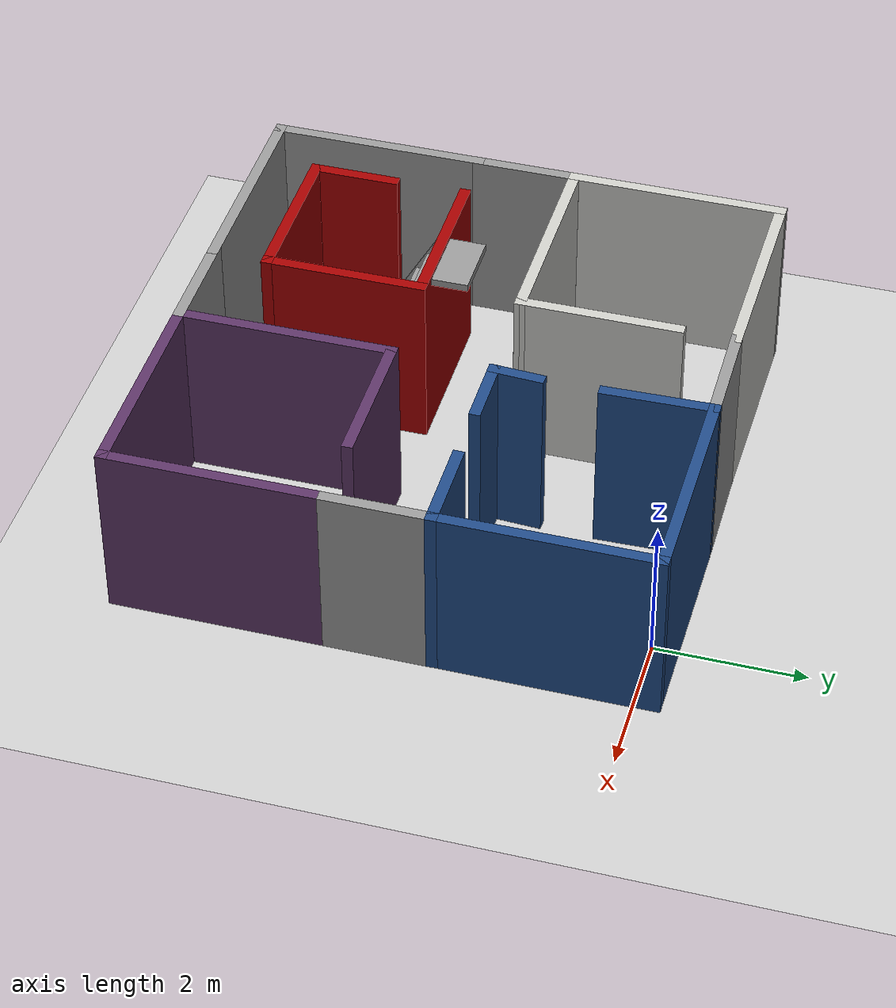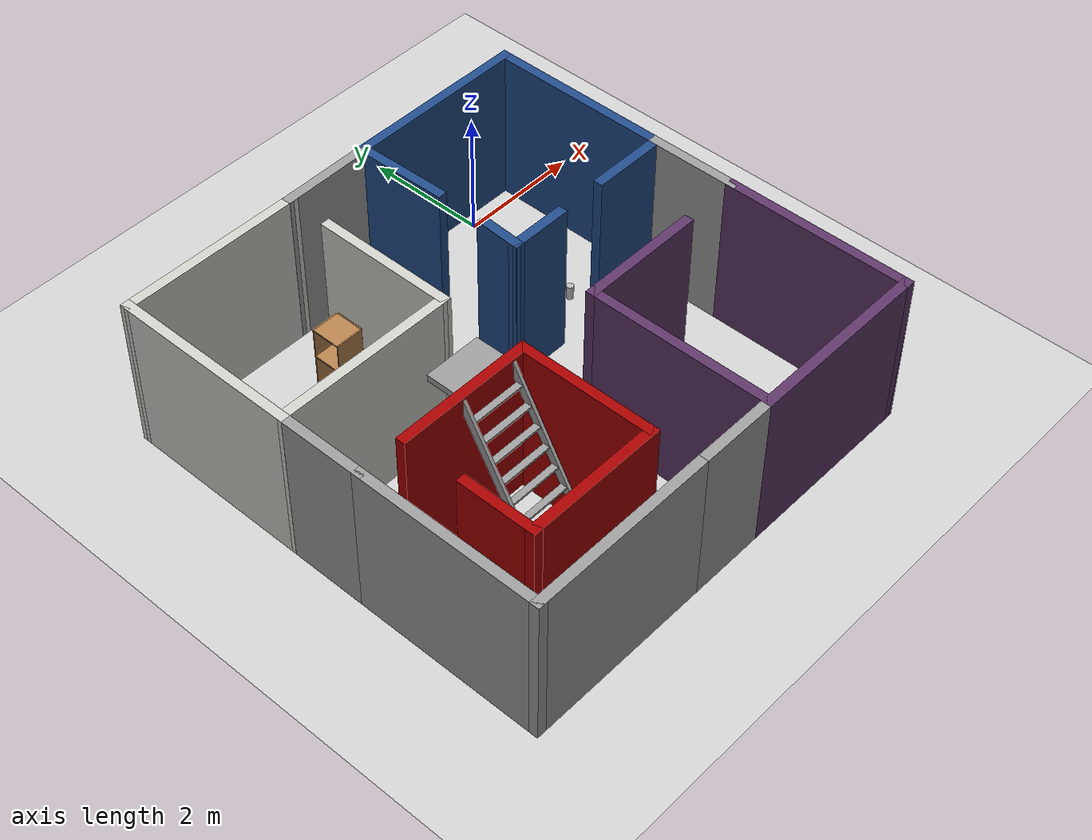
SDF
<sdf version="1.6">
 <world name="default">
  <plugin name="hello" filename="libhello.so"/>
  <gravity>0 0 -9.8</gravity>
  <magnetic_field>6e-06 2.3e-05 -4.2e-05</magnetic_field>
  <atmosphere type="adiabatic"/>
  <physics name="default_physics" default="0" type="ode">
   <max_step_size>0.001</max_step_size>
   <real_time_factor>1</real_time_factor>
   <real_time_update_rate>1000</real_time_update_rate>
  </physics>
  <scene><ambient>0.4 0.4 0.4 1</ambient><background>0.7 0.7 0.7 1</background><shadows>1</shadows></scene>
  <spherical_coordinates>
   <surface_model>EARTH_WGS84</surface_model>
   <latitude_deg>0</latitude_deg>
   <longitude_deg>0</longitude_deg>
   <elevation>0</elevation>
   <heading_deg>0</heading_deg>
  </spherical_coordinates>
  <model name="apartment">
   <link name="Wall_20">
    <pose>-3.52477 2.09918 0 0 0 -1.5708</pose>
    <visual name="Wall_20_Visual">
     <pose>0 0 1.25 0 -0 0</pose>
     <geometry><box><size>3 0.15 2.5</size></box></geometry>
     <material>
      <script><uri>file://media/materials/scripts/gazebo.material</uri><name>Gazebo/CeilingTiled</name></script>
      <ambient>0.435294 0.796078 0.67451 1</ambient>
      <shader type="pixel"/>
     </material>
     <meta><layer>0</layer></meta>
    </visual>
    <collision name="Wall_20_Collision">
     <pose>0 0 1.25 0 -0 0</pose>
     <geometry><box><size>3 0.15 2.5</size></box></geometry>
     <surface>
      <friction>
       <ode><mu>1</mu><mu2>1</mu2><fdir1>0 0 0</fdir1><slip1>0</slip1><slip2>0</slip2></ode>
       <torsional>
        <coefficient>1</coefficient>
        <patch_radius>0</patch_radius>
        <surface_radius>0</surface_radius>
        <use_patch_radius>1</use_patch_radius>
        <ode><slip>0</slip></ode>
       </torsional>
      </friction>
      <bounce><restitution_coefficient>0</restitution_coefficient><threshold>1e+06</threshold></bounce>
      <contact>
       <collide_without_contact>0</collide_without_contact>
       <collide_without_contact_bitmask>1</collide_without_contact_bitmask>
       <collide_bitmask>1</collide_bitmask>
       <ode>
        <soft_cfm>0</soft_cfm>
        <soft_erp>0.2</soft_erp>
        <kp>1e+13</kp>
        <kd>1</kd>
        <max_vel>0.01</max_vel>
        <min_depth>0</min_depth>
       </ode>
       <bullet>
        <split_impulse>1</split_impulse>
        <split_impulse_penetration_threshold>-0.01</split_impulse_penetration_threshold>
        <soft_cfm>0</soft_cfm>
        <soft_erp>0.2</soft_erp>
        <kp>1e+13</kp>
        <kd>1</kd>
       </bullet>
      </contact>
     </surface>
    </collision>
   </link>
   <link name="Wall_21">
    <pose>-2.126 0.665439 0 0 0 -0.006252</pose>
    <visual name="Wall_21_Visual">
     <pose>0 0 1.25 0 -0 0</pose>
     <geometry><box><size>2.94758 0.15 2.5</size></box></geometry>
     <material>
      <script><uri>file://media/materials/scripts/gazebo.material</uri><name>Gazebo/CeilingTiled</name></script>
      <ambient>0.435294 0.796078 0.67451 1</ambient>
      <shader type="pixel"/>
     </material>
     <meta><layer>0</layer></meta>
    </visual>
    <collision name="Wall_21_Collision">
     <pose>0 0 1.25 0 -0 0</pose>
     <geometry><box><size>2.94758 0.15 2.5</size></box></geometry>
     <surface>
      <friction>
       <ode><mu>1</mu><mu2>1</mu2><fdir1>0 0 0</fdir1><slip1>0</slip1><slip2>0</slip2></ode>
       <torsional>
        <coefficient>1</coefficient>
        <patch_radius>0</patch_radius>
        <surface_radius>0</surface_radius>
        <use_patch_radius>1</use_patch_radius>
        <ode><slip>0</slip></ode>
       </torsional>
      </friction>
      <bounce><restitution_coefficient>0</restitution_coefficient><threshold>1e+06</threshold></bounce>
      <contact>
       <collide_without_contact>0</collide_without_contact>
       <collide_without_contact_bitmask>1</collide_without_contact_bitmask>
       <collide_bitmask>1</collide_bitmask>
       <ode>
        <soft_cfm>0</soft_cfm>
        <soft_erp>0.2</soft_erp>
        <kp>1e+13</kp>
        <kd>1</kd>
        <max_vel>0.01</max_vel>
        <min_depth>0</min_depth>
       </ode>
       <bullet>
        <split_impulse>1</split_impulse>
        <split_impulse_penetration_threshold>-0.01</split_impulse_penetration_threshold>
        <soft_cfm>0</soft_cfm>
        <soft_erp>0.2</soft_erp>
        <kp>1e+13</kp>
        <kd>1</kd>
       </bullet>
      </contact>
     </surface>
    </collision>
   </link>
   <link name="Wall_23">
    <pose>-2.126 3.51544 0 0 -0 3.13534</pose>
    <visual name="Wall_23_Visual">
     <pose>0 0 1.25 0 -0 0</pose>
     <geometry><box><size>2.94758 0.15 2.5</size></box></geometry>
     <material>
      <script><uri>file://media/materials/scripts/gazebo.material</uri><name>Gazebo/CeilingTiled</name></script>
      <ambient>0.435294 0.796078 0.67451 1</ambient>
      <shader type="pixel"/>
     </material>
     <meta><layer>0</layer></meta>
    </visual>
    <collision name="Wall_23_Collision">
     <pose>0 0 1.25 0 -0 0</pose>
     <geometry><box><size>2.94758 0.15 2.5</size></box></geometry>
     <surface>
      <friction>
       <ode><mu>1</mu><mu2>1</mu2><fdir1>0 0 0</fdir1><slip1>0</slip1><slip2>0</slip2></ode>
       <torsional>
        <coefficient>1</coefficient>
        <patch_radius>0</patch_radius>
        <surface_radius>0</surface_radius>
        <use_patch_radius>1</use_patch_radius>
        <ode><slip>0</slip></ode>
       </torsional>
      </friction>
      <bounce><restitution_coefficient>0</restitution_coefficient><threshold>1e+06</threshold></bounce>
      <contact>
       <collide_without_contact>0</collide_without_contact>
       <collide_without_contact_bitmask>1</collide_without_contact_bitmask>
       <collide_bitmask>1</collide_bitmask>
       <ode>
        <soft_cfm>0</soft_cfm>
        <soft_erp>0.2</soft_erp>
        <kp>1e+13</kp>
        <kd>1</kd>
        <max_vel>0.01</max_vel>
        <min_depth>0</min_depth>
       </ode>
       <bullet>
        <split_impulse>1</split_impulse>
        <split_impulse_penetration_threshold>-0.01</split_impulse_penetration_threshold>
        <soft_cfm>0</soft_cfm>
        <soft_erp>0.2</soft_erp>
        <kp>1e+13</kp>
        <kd>1</kd>
       </bullet>
      </contact>
     </surface>
    </collision>
   </link>
   <link name="Wall_25">
    <pose>-3.52477 -0.000816 0 0 0 -1.5708</pose>
    <visual name="Wall_25_Visual">
     <pose>0 0 1.25 0 -0 0</pose>
     <geometry><box><size>1.5 0.15 2.5</size></box></geometry>
     <material>
      <script><uri>file://media/materials/scripts/gazebo.material</uri><name>Gazebo/Grey</name></script>
      <ambient>0.729412 0.741176 0.713726 1</ambient>
      <shader type="pixel"/>
     </material>
     <meta><layer>0</layer></meta>
    </visual>
    <collision name="Wall_25_Collision">
     <pose>0 0 1.25 0 -0 0</pose>
     <geometry><box><size>1.5 0.15 2.5</size></box></geometry>
     <surface>
      <friction>
       <ode><mu>1</mu><mu2>1</mu2><fdir1>0 0 0</fdir1><slip1>0</slip1><slip2>0</slip2></ode>
       <torsional>
        <coefficient>1</coefficient>
        <patch_radius>0</patch_radius>
        <surface_radius>0</surface_radius>
        <use_patch_radius>1</use_patch_radius>
        <ode><slip>0</slip></ode>
       </torsional>
      </friction>
      <bounce><restitution_coefficient>0</restitution_coefficient><threshold>1e+06</threshold></bounce>
      <contact>
       <collide_without_contact>0</collide_without_contact>
       <collide_without_contact_bitmask>1</collide_without_contact_bitmask>
       <collide_bitmask>1</collide_bitmask>
       <ode>
        <soft_cfm>0</soft_cfm>
        <soft_erp>0.2</soft_erp>
        <kp>1e+13</kp>
        <kd>1</kd>
        <max_vel>0.01</max_vel>
        <min_depth>0</min_depth>
       </ode>
       <bullet>
        <split_impulse>1</split_impulse>
        <split_impulse_penetration_threshold>-0.01</split_impulse_penetration_threshold>
        <soft_cfm>0</soft_cfm>
        <soft_erp>0.2</soft_erp>
        <kp>1e+13</kp>
        <kd>1</kd>
       </bullet>
      </contact>
     </surface>
    </collision>
   </link>
   <link name="Wall_29">
    <pose>-2.09977 -3.52582 0 0 -0 3.14159</pose>
    <visual name="Wall_29_Visual">
     <pose>0 0 1.25 0 -0 0</pose>
     <geometry><box><size>3 0.15 2.5</size></box></geometry>
     <material>
      <script><uri>file://media/materials/scripts/gazebo.material</uri><name>Gazebo/Grey</name></script>
      <ambient>0.729412 0.741176 0.713726 1</ambient>
      <shader type="pixel"/>
     </material>
     <meta><layer>0</layer></meta>
    </visual>
    <collision name="Wall_29_Collision">
     <pose>0 0 1.25 0 -0 0</pose>
     <geometry><box><size>3 0.15 2.5</size></box></geometry>
     <surface>
      <friction>
       <ode><mu>1</mu><mu2>1</mu2><fdir1>0 0 0</fdir1><slip1>0</slip1><slip2>0</slip2></ode>
       <torsional>
        <coefficient>1</coefficient>
        <patch_radius>0</patch_radius>
        <surface_radius>0</surface_radius>
        <use_patch_radius>1</use_patch_radius>
        <ode><slip>0</slip></ode>
       </torsional>
      </friction>
      <bounce><restitution_coefficient>0</restitution_coefficient><threshold>1e+06</threshold></bounce>
      <contact>
       <collide_without_contact>0</collide_without_contact>
       <collide_without_contact_bitmask>1</collide_without_contact_bitmask>
       <collide_bitmask>1</collide_bitmask>
       <ode>
        <soft_cfm>0</soft_cfm>
        <soft_erp>0.2</soft_erp>
        <kp>1e+13</kp>
        <kd>1</kd>
        <max_vel>0.01</max_vel>
        <min_depth>0</min_depth>
       </ode>
       <bullet>
        <split_impulse>1</split_impulse>
        <split_impulse_penetration_threshold>-0.01</split_impulse_penetration_threshold>
        <soft_cfm>0</soft_cfm>
        <soft_erp>0.2</soft_erp>
        <kp>1e+13</kp>
        <kd>1</kd>
       </bullet>
      </contact>
     </surface>
    </collision>
   </link>
   <link name="Wall_30">
    <pose>-3.52477 -2.10082 0 0 -0 1.5708</pose>
    <visual name="Wall_30_Visual">
     <pose>0 0 1.25 0 -0 0</pose>
     <geometry><box><size>3 0.15 2.5</size></box></geometry>
     <material>
      <script><uri>file://media/materials/scripts/gazebo.material</uri><name>Gazebo/Grey</name></script>
      <ambient>0.729412 0.741176 0.713726 1</ambient>
      <shader type="pixel"/>
     </material>
     <meta><layer>0</layer></meta>
    </visual>
    <collision name="Wall_30_Collision">
     <pose>0 0 1.25 0 -0 0</pose>
     <geometry><box><size>3 0.15 2.5</size></box></geometry>
     <surface>
      <friction>
       <ode><mu>1</mu><mu2>1</mu2><fdir1>0 0 0</fdir1><slip1>0</slip1><slip2>0</slip2></ode>
       <torsional>
        <coefficient>1</coefficient>
        <patch_radius>0</patch_radius>
        <surface_radius>0</surface_radius>
        <use_patch_radius>1</use_patch_radius>
        <ode><slip>0</slip></ode>
       </torsional>
      </friction>
      <bounce><restitution_coefficient>0</restitution_coefficient><threshold>1e+06</threshold></bounce>
      <contact>
       <collide_without_contact>0</collide_without_contact>
       <collide_without_contact_bitmask>1</collide_without_contact_bitmask>
       <collide_bitmask>1</collide_bitmask>
       <ode>
        <soft_cfm>0</soft_cfm>
        <soft_erp>0.2</soft_erp>
        <kp>1e+13</kp>
        <kd>1</kd>
        <max_vel>0.01</max_vel>
        <min_depth>0</min_depth>
       </ode>
       <bullet>
        <split_impulse>1</split_impulse>
        <split_impulse_penetration_threshold>-0.01</split_impulse_penetration_threshold>
        <soft_cfm>0</soft_cfm>
        <soft_erp>0.2</soft_erp>
        <kp>1e+13</kp>
        <kd>1</kd>
       </bullet>
      </contact>
     </surface>
    </collision>
   </link>
   <link name="Wall_32">
    <pose>-0.026002 3.51544 0 0 -0 0.01247</pose>
    <visual name="Wall_32_Visual">
     <pose>0 0 1.25 0 -0 0</pose>
     <geometry><box><size>1.55258 0.15 2.5</size></box></geometry>
     <material>
      <script><uri>file://media/materials/scripts/gazebo.material</uri><name>Gazebo/Grey</name></script>
      <ambient>0.729412 0.741176 0.713726 1</ambient>
      <shader type="pixel"/>
     </material>
     <meta><layer>0</layer></meta>
    </visual>
    <collision name="Wall_32_Collision">
     <pose>0 0 1.25 0 -0 0</pose>
     <geometry><box><size>1.55258 0.15 2.5</size></box></geometry>
     <surface>
      <friction>
       <ode><mu>1</mu><mu2>1</mu2><fdir1>0 0 0</fdir1><slip1>0</slip1><slip2>0</slip2></ode>
       <torsional>
        <coefficient>1</coefficient>
        <patch_radius>0</patch_radius>
        <surface_radius>0</surface_radius>
        <use_patch_radius>1</use_patch_radius>
        <ode><slip>0</slip></ode>
       </torsional>
      </friction>
      <bounce><restitution_coefficient>0</restitution_coefficient><threshold>1e+06</threshold></bounce>
      <contact>
       <collide_without_contact>0</collide_without_contact>
       <collide_without_contact_bitmask>1</collide_without_contact_bitmask>
       <collide_bitmask>1</collide_bitmask>
       <ode>
        <soft_cfm>0</soft_cfm>
        <soft_erp>0.2</soft_erp>
        <kp>1e+13</kp>
        <kd>1</kd>
        <max_vel>0.01</max_vel>
        <min_depth>0</min_depth>
       </ode>
       <bullet>
        <split_impulse>1</split_impulse>
        <split_impulse_penetration_threshold>-0.01</split_impulse_penetration_threshold>
        <soft_cfm>0</soft_cfm>
        <soft_erp>0.2</soft_erp>
        <kp>1e+13</kp>
        <kd>1</kd>
       </bullet>
      </contact>
     </surface>
    </collision>
   </link>
   <link name="Wall_33">
    <pose>2.10023 3.52418 0 0 -0 0</pose>
    <visual name="Wall_33_Visual">
     <pose>0 0 1.25 0 -0 0</pose>
     <geometry><box><size>3 0.15 2.5</size></box></geometry>
     <material>
      <script><uri>file://media/materials/scripts/gazebo.material</uri><name>Gazebo/Grey</name></script>
      <ambient>0.12549 0.290196 0.529412 1</ambient>
      <shader type="pixel"/>
     </material>
     <meta><layer>0</layer></meta>
    </visual>
    <collision name="Wall_33_Collision">
     <pose>0 0 1.25 0 -0 0</pose>
     <geometry><box><size>3 0.15 2.5</size></box></geometry>
     <surface>
      <friction>
       <ode><mu>1</mu><mu2>1</mu2><fdir1>0 0 0</fdir1><slip1>0</slip1><slip2>0</slip2></ode>
       <torsional>
        <coefficient>1</coefficient>
        <patch_radius>0</patch_radius>
        <surface_radius>0</surface_radius>
        <use_patch_radius>1</use_patch_radius>
        <ode><slip>0</slip></ode>
       </torsional>
      </friction>
      <bounce><restitution_coefficient>0</restitution_coefficient><threshold>1e+06</threshold></bounce>
      <contact>
       <collide_without_contact>0</collide_without_contact>
       <collide_without_contact_bitmask>1</collide_without_contact_bitmask>
       <collide_bitmask>1</collide_bitmask>
       <ode>
        <soft_cfm>0</soft_cfm>
        <soft_erp>0.2</soft_erp>
        <kp>1e+13</kp>
        <kd>1</kd>
        <max_vel>0.01</max_vel>
        <min_depth>0</min_depth>
       </ode>
       <bullet>
        <split_impulse>1</split_impulse>
        <split_impulse_penetration_threshold>-0.01</split_impulse_penetration_threshold>
        <soft_cfm>0</soft_cfm>
        <soft_erp>0.2</soft_erp>
        <kp>1e+13</kp>
        <kd>1</kd>
       </bullet>
      </contact>
     </surface>
    </collision>
   </link>
   <link name="Wall_34">
    <pose>3.52523 2.09918 0 0 0 -1.5708</pose>
    <visual name="Wall_34_Visual">
     <pose>0 0 1.25 0 -0 0</pose>
     <geometry><box><size>3 0.15 2.5</size></box></geometry>
     <material>
      <script><uri>file://media/materials/scripts/gazebo.material</uri><name>Gazebo/Grey</name></script>
      <ambient>0.12549 0.290196 0.529412 1</ambient>
      <shader type="pixel"/>
     </material>
     <meta><layer>0</layer></meta>
    </visual>
    <collision name="Wall_34_Collision">
     <pose>0 0 1.25 0 -0 0</pose>
     <geometry><box><size>3 0.15 2.5</size></box></geometry>
     <surface>
      <friction>
       <ode><mu>1</mu><mu2>1</mu2><fdir1>0 0 0</fdir1><slip1>0</slip1><slip2>0</slip2></ode>
       <torsional>
        <coefficient>1</coefficient>
        <patch_radius>0</patch_radius>
        <surface_radius>0</surface_radius>
        <use_patch_radius>1</use_patch_radius>
        <ode><slip>0</slip></ode>
       </torsional>
      </friction>
      <bounce><restitution_coefficient>0</restitution_coefficient><threshold>1e+06</threshold></bounce>
      <contact>
       <collide_without_contact>0</collide_without_contact>
       <collide_without_contact_bitmask>1</collide_without_contact_bitmask>
       <collide_bitmask>1</collide_bitmask>
       <ode>
        <soft_cfm>0</soft_cfm>
        <soft_erp>0.2</soft_erp>
        <kp>1e+13</kp>
        <kd>1</kd>
        <max_vel>0.01</max_vel>
        <min_depth>0</min_depth>
       </ode>
       <bullet>
        <split_impulse>1</split_impulse>
        <split_impulse_penetration_threshold>-0.01</split_impulse_penetration_threshold>
        <soft_cfm>0</soft_cfm>
        <soft_erp>0.2</soft_erp>
        <kp>1e+13</kp>
        <kd>1</kd>
       </bullet>
      </contact>
     </surface>
    </collision>
   </link>
   <link name="Wall_38">
    <pose>0.000234 -3.52582 0 0 -0 0</pose>
    <visual name="Wall_38_Visual">
     <pose>0 0 1.25 0 -0 0</pose>
     <geometry><box><size>1.5 0.15 2.5</size></box></geometry>
     <material>
      <script><uri>file://media/materials/scripts/gazebo.material</uri><name>Gazebo/Grey</name></script>
      <ambient>0.729412 0.741176 0.713726 1</ambient>
      <shader type="pixel"/>
     </material>
     <meta><layer>0</layer></meta>
    </visual>
    <collision name="Wall_38_Collision">
     <pose>0 0 1.25 0 -0 0</pose>
     <geometry><box><size>1.5 0.15 2.5</size></box></geometry>
     <surface>
      <friction>
       <ode><mu>1</mu><mu2>1</mu2><fdir1>0 0 0</fdir1><slip1>0</slip1><slip2>0</slip2></ode>
       <torsional>
        <coefficient>1</coefficient>
        <patch_radius>0</patch_radius>
        <surface_radius>0</surface_radius>
        <use_patch_radius>1</use_patch_radius>
        <ode><slip>0</slip></ode>
       </torsional>
      </friction>
      <bounce><restitution_coefficient>0</restitution_coefficient><threshold>1e+06</threshold></bounce>
      <contact>
       <collide_without_contact>0</collide_without_contact>
       <collide_without_contact_bitmask>1</collide_without_contact_bitmask>
       <collide_bitmask>1</collide_bitmask>
       <ode>
        <soft_cfm>0</soft_cfm>
        <soft_erp>0.2</soft_erp>
        <kp>1e+13</kp>
        <kd>1</kd>
        <max_vel>0.01</max_vel>
        <min_depth>0</min_depth>
       </ode>
       <bullet>
        <split_impulse>1</split_impulse>
        <split_impulse_penetration_threshold>-0.01</split_impulse_penetration_threshold>
        <soft_cfm>0</soft_cfm>
        <soft_erp>0.2</soft_erp>
        <kp>1e+13</kp>
        <kd>1</kd>
       </bullet>
      </contact>
     </surface>
    </collision>
   </link>
   <link name="Wall_39">
    <pose>2.10023 -3.52582 0 0 -0 0</pose>
    <visual name="Wall_39_Visual">
     <pose>0 0 1.25 0 -0 0</pose>
     <geometry><box><size>3 0.15 2.5</size></box></geometry>
     <material>
      <script><uri>file://media/materials/scripts/gazebo.material</uri><name>Gazebo/Grey</name></script>
      <ambient>0.360784 0.207843 0.4 1</ambient>
      <shader type="pixel"/>
     </material>
     <meta><layer>0</layer></meta>
    </visual>
    <collision name="Wall_39_Collision">
     <pose>0 0 1.25 0 -0 0</pose>
     <geometry><box><size>3 0.15 2.5</size></box></geometry>
     <surface>
      <friction>
       <ode><mu>1</mu><mu2>1</mu2><fdir1>0 0 0</fdir1><slip1>0</slip1><slip2>0</slip2></ode>
       <torsional>
        <coefficient>1</coefficient>
        <patch_radius>0</patch_radius>
        <surface_radius>0</surface_radius>
        <use_patch_radius>1</use_patch_radius>
        <ode><slip>0</slip></ode>
       </torsional>
      </friction>
      <bounce><restitution_coefficient>0</restitution_coefficient><threshold>1e+06</threshold></bounce>
      <contact>
       <collide_without_contact>0</collide_without_contact>
       <collide_without_contact_bitmask>1</collide_without_contact_bitmask>
       <collide_bitmask>1</collide_bitmask>
       <ode>
        <soft_cfm>0</soft_cfm>
        <soft_erp>0.2</soft_erp>
        <kp>1e+13</kp>
        <kd>1</kd>
        <max_vel>0.01</max_vel>
        <min_depth>0</min_depth>
       </ode>
       <bullet>
        <split_impulse>1</split_impulse>
        <split_impulse_penetration_threshold>-0.01</split_impulse_penetration_threshold>
        <soft_cfm>0</soft_cfm>
        <soft_erp>0.2</soft_erp>
        <kp>1e+13</kp>
        <kd>1</kd>
       </bullet>
      </contact>
     </surface>
    </collision>
   </link>
   <link name="Wall_40">
    <pose>3.52523 -2.10082 0 0 -0 1.5708</pose>
    <visual name="Wall_40_Visual">
     <pose>0 0 1.25 0 -0 0</pose>
     <geometry><box><size>3 0.15 2.5</size></box></geometry>
     <material>
      <script><uri>file://media/materials/scripts/gazebo.material</uri><name>Gazebo/Grey</name></script>
      <ambient>0.360784 0.207843 0.4 1</ambient>
      <shader type="pixel"/>
     </material>
     <meta><layer>0</layer></meta>
    </visual>
    <collision name="Wall_40_Collision">
     <pose>0 0 1.25 0 -0 0</pose>
     <geometry><box><size>3 0.15 2.5</size></box></geometry>
     <surface>
      <friction>
       <ode><mu>1</mu><mu2>1</mu2><fdir1>0 0 0</fdir1><slip1>0</slip1><slip2>0</slip2></ode>
       <torsional>
        <coefficient>1</coefficient>
        <patch_radius>0</patch_radius>
        <surface_radius>0</surface_radius>
        <use_patch_radius>1</use_patch_radius>
        <ode><slip>0</slip></ode>
       </torsional>
      </friction>
      <bounce><restitution_coefficient>0</restitution_coefficient><threshold>1e+06</threshold></bounce>
      <contact>
       <collide_without_contact>0</collide_without_contact>
       <collide_without_contact_bitmask>1</collide_without_contact_bitmask>
       <collide_bitmask>1</collide_bitmask>
       <ode>
        <soft_cfm>0</soft_cfm>
        <soft_erp>0.2</soft_erp>
        <kp>1e+13</kp>
        <kd>1</kd>
        <max_vel>0.01</max_vel>
        <min_depth>0</min_depth>
       </ode>
       <bullet>
        <split_impulse>1</split_impulse>
        <split_impulse_penetration_threshold>-0.01</split_impulse_penetration_threshold>
        <soft_cfm>0</soft_cfm>
        <soft_erp>0.2</soft_erp>
        <kp>1e+13</kp>
        <kd>1</kd>
       </bullet>
      </contact>
     </surface>
    </collision>
   </link>
   <link name="Wall_42">
    <pose>0.675234 -2.10082 0 0 0 -1.5708</pose>
    <visual name="Wall_42_Visual">
     <pose>0 0 1.25 0 -0 0</pose>
     <geometry><box><size>3 0.15 2.5</size></box></geometry>
     <material>
      <script><uri>file://media/materials/scripts/gazebo.material</uri><name>Gazebo/Grey</name></script>
      <ambient>0.360784 0.207843 0.4 1</ambient>
      <shader type="pixel"/>
     </material>
     <meta><layer>0</layer></meta>
    </visual>
    <collision name="Wall_42_Collision">
     <pose>0 0 1.25 0 -0 0</pose>
     <geometry><box><size>3 0.15 2.5</size></box></geometry>
     <surface>
      <friction>
       <ode><mu>1</mu><mu2>1</mu2><fdir1>0 0 0</fdir1><slip1>0</slip1><slip2>0</slip2></ode>
       <torsional>
        <coefficient>1</coefficient>
        <patch_radius>0</patch_radius>
        <surface_radius>0</surface_radius>
        <use_patch_radius>1</use_patch_radius>
        <ode><slip>0</slip></ode>
       </torsional>
      </friction>
      <bounce><restitution_coefficient>0</restitution_coefficient><threshold>1e+06</threshold></bounce>
      <contact>
       <collide_without_contact>0</collide_without_contact>
       <collide_without_contact_bitmask>1</collide_without_contact_bitmask>
       <collide_bitmask>1</collide_bitmask>
       <ode>
        <soft_cfm>0</soft_cfm>
        <soft_erp>0.2</soft_erp>
        <kp>1e+13</kp>
        <kd>1</kd>
        <max_vel>0.01</max_vel>
        <min_depth>0</min_depth>
       </ode>
       <bullet>
        <split_impulse>1</split_impulse>
        <split_impulse_penetration_threshold>-0.01</split_impulse_penetration_threshold>
        <soft_cfm>0</soft_cfm>
        <soft_erp>0.2</soft_erp>
        <kp>1e+13</kp>
        <kd>1</kd>
       </bullet>
      </contact>
     </surface>
    </collision>
   </link>
   <link name="Wall_44">
    <pose>3.52523 -0.000816 0 0 -0 1.5708</pose>
    <visual name="Wall_44_Visual">
     <pose>0 0 1.25 0 -0 0</pose>
     <geometry><box><size>1.5 0.15 2.5</size></box></geometry>
     <material>
      <script><uri>file://media/materials/scripts/gazebo.material</uri><name>Gazebo/Grey</name></script>
      <ambient>0.729412 0.741176 0.713726 1</ambient>
      <shader type="pixel"/>
     </material>
     <meta><layer>0</layer></meta>
    </visual>
    <collision name="Wall_44_Collision">
     <pose>0 0 1.25 0 -0 0</pose>
     <geometry><box><size>1.5 0.15 2.5</size></box></geometry>
     <surface>
      <friction>
       <ode><mu>1</mu><mu2>1</mu2><fdir1>0 0 0</fdir1><slip1>0</slip1><slip2>0</slip2></ode>
       <torsional>
        <coefficient>1</coefficient>
        <patch_radius>0</patch_radius>
        <surface_radius>0</surface_radius>
        <use_patch_radius>1</use_patch_radius>
        <ode><slip>0</slip></ode>
       </torsional>
      </friction>
      <bounce><restitution_coefficient>0</restitution_coefficient><threshold>1e+06</threshold></bounce>
      <contact>
       <collide_without_contact>0</collide_without_contact>
       <collide_without_contact_bitmask>1</collide_without_contact_bitmask>
       <collide_bitmask>1</collide_bitmask>
       <ode>
        <soft_cfm>0</soft_cfm>
        <soft_erp>0.2</soft_erp>
        <kp>1e+13</kp>
        <kd>1</kd>
        <max_vel>0.01</max_vel>
        <min_depth>0</min_depth>
       </ode>
       <bullet>
        <split_impulse>1</split_impulse>
        <split_impulse_penetration_threshold>-0.01</split_impulse_penetration_threshold>
        <soft_cfm>0</soft_cfm>
        <soft_erp>0.2</soft_erp>
        <kp>1e+13</kp>
        <kd>1</kd>
       </bullet>
      </contact>
     </surface>
    </collision>
   </link>
   <link name="Wall_46">
    <pose>1.60023 -0.675816 0 0 -0 0</pose>
    <visual name="Wall_46_Visual">
     <pose>0 0 1.25 0 -0 0</pose>
     <geometry><box><size>2 0.15 2.5</size></box></geometry>
     <material>
      <script><uri>file://media/materials/scripts/gazebo.material</uri><name>Gazebo/Grey</name></script>
      <ambient>0.360784 0.207843 0.4 1</ambient>
      <shader type="pixel"/>
     </material>
     <meta><layer>0</layer></meta>
    </visual>
    <collision name="Wall_46_Collision">
     <pose>0 0 1.25 0 -0 0</pose>
     <geometry><box><size>2 0.15 2.5</size></box></geometry>
     <surface>
      <friction>
       <ode><mu>1</mu><mu2>1</mu2><fdir1>0 0 0</fdir1><slip1>0</slip1><slip2>0</slip2></ode>
       <torsional>
        <coefficient>1</coefficient>
        <patch_radius>0</patch_radius>
        <surface_radius>0</surface_radius>
        <use_patch_radius>1</use_patch_radius>
        <ode><slip>0</slip></ode>
       </torsional>
      </friction>
      <bounce><restitution_coefficient>0</restitution_coefficient><threshold>1e+06</threshold></bounce>
      <contact>
       <collide_without_contact>0</collide_without_contact>
       <collide_without_contact_bitmask>1</collide_without_contact_bitmask>
       <collide_bitmask>1</collide_bitmask>
       <ode>
        <soft_cfm>0</soft_cfm>
        <soft_erp>0.2</soft_erp>
        <kp>1e+13</kp>
        <kd>1</kd>
        <max_vel>0.01</max_vel>
        <min_depth>0</min_depth>
       </ode>
       <bullet>
        <split_impulse>1</split_impulse>
        <split_impulse_penetration_threshold>-0.01</split_impulse_penetration_threshold>
        <soft_cfm>0</soft_cfm>
        <soft_erp>0.2</soft_erp>
        <kp>1e+13</kp>
        <kd>1</kd>
       </bullet>
      </contact>
     </surface>
    </collision>
   </link>
   <link name="Wall_48">
    <pose>1.10023 0.674184 0 0 -0 0</pose>
    <visual name="Wall_48_Visual">
     <pose>0 0 1.25 0 -0 0</pose>
     <geometry><box><size>1 0.15 2.5</size></box></geometry>
     <material>
      <script><uri>file://media/materials/scripts/gazebo.material</uri><name>Gazebo/Grey</name></script>
      <ambient>0.12549 0.290196 0.529412 1</ambient>
      <shader type="pixel"/>
     </material>
     <meta><layer>0</layer></meta>
    </visual>
    <collision name="Wall_48_Collision">
     <pose>0 0 1.25 0 -0 0</pose>
     <geometry><box><size>1 0.15 2.5</size></box></geometry>
     <surface>
      <friction>
       <ode><mu>1</mu><mu2>1</mu2><fdir1>0 0 0</fdir1><slip1>0</slip1><slip2>0</slip2></ode>
       <torsional>
        <coefficient>1</coefficient>
        <patch_radius>0</patch_radius>
        <surface_radius>0</surface_radius>
        <use_patch_radius>1</use_patch_radius>
        <ode><slip>0</slip></ode>
       </torsional>
      </friction>
      <bounce><restitution_coefficient>0</restitution_coefficient><threshold>1e+06</threshold></bounce>
      <contact>
       <collide_without_contact>0</collide_without_contact>
       <collide_without_contact_bitmask>1</collide_without_contact_bitmask>
       <collide_bitmask>1</collide_bitmask>
       <ode>
        <soft_cfm>0</soft_cfm>
        <soft_erp>0.2</soft_erp>
        <kp>1e+13</kp>
        <kd>1</kd>
        <max_vel>0.01</max_vel>
        <min_depth>0</min_depth>
       </ode>
       <bullet>
        <split_impulse>1</split_impulse>
        <split_impulse_penetration_threshold>-0.01</split_impulse_penetration_threshold>
        <soft_cfm>0</soft_cfm>
        <soft_erp>0.2</soft_erp>
        <kp>1e+13</kp>
        <kd>1</kd>
       </bullet>
      </contact>
     </surface>
    </collision>
   </link>
   <link name="Wall_51">
    <pose>2.95023 0.674184 0 0 -0 0</pose>
    <visual name="Wall_51_Visual">
     <pose>0 0 1.25 0 -0 0</pose>
     <geometry><box><size>1.3 0.15 2.5</size></box></geometry>
     <material>
      <script><uri>file://media/materials/scripts/gazebo.material</uri><name>Gazebo/Grey</name></script>
      <ambient>0.12549 0.290196 0.529412 1</ambient>
      <shader type="pixel"/>
     </material>
     <meta><layer>0</layer></meta>
    </visual>
    <collision name="Wall_51_Collision">
     <pose>0 0 1.25 0 -0 0</pose>
     <geometry><box><size>1.3 0.15 2.5</size></box></geometry>
     <surface>
      <friction>
       <ode><mu>1</mu><mu2>1</mu2><fdir1>0 0 0</fdir1><slip1>0</slip1><slip2>0</slip2></ode>
       <torsional>
        <coefficient>1</coefficient>
        <patch_radius>0</patch_radius>
        <surface_radius>0</surface_radius>
        <use_patch_radius>1</use_patch_radius>
        <ode><slip>0</slip></ode>
       </torsional>
      </friction>
      <bounce><restitution_coefficient>0</restitution_coefficient><threshold>1e+06</threshold></bounce>
      <contact>
       <collide_without_contact>0</collide_without_contact>
       <collide_without_contact_bitmask>1</collide_without_contact_bitmask>
       <collide_bitmask>1</collide_bitmask>
       <ode>
        <soft_cfm>0</soft_cfm>
        <soft_erp>0.2</soft_erp>
        <kp>1e+13</kp>
        <kd>1</kd>
        <max_vel>0.01</max_vel>
        <min_depth>0</min_depth>
       </ode>
       <bullet>
        <split_impulse>1</split_impulse>
        <split_impulse_penetration_threshold>-0.01</split_impulse_penetration_threshold>
        <soft_cfm>0</soft_cfm>
        <soft_erp>0.2</soft_erp>
        <kp>1e+13</kp>
        <kd>1</kd>
       </bullet>
      </contact>
     </surface>
    </collision>
   </link>
   <link name="Wall_53">
    <pose>-0.727237 1.70669 0 0 -0 1.5708</pose>
    <visual name="Wall_53_Visual">
     <pose>0 0 1.25 0 -0 0</pose>
     <geometry><box><size>2.25 0.15 2.5</size></box></geometry>
     <material>
      <script><uri>file://media/materials/scripts/gazebo.material</uri><name>Gazebo/CeilingTiled</name></script>
      <ambient>0.435294 0.796078 0.67451 1</ambient>
      <shader type="pixel"/>
     </material>
     <meta><layer>0</layer></meta>
    </visual>
    <collision name="Wall_53_Collision">
     <pose>0 0 1.25 0 -0 0</pose>
     <geometry><box><size>2.25 0.15 2.5</size></box></geometry>
     <surface>
      <friction>
       <ode><mu>1</mu><mu2>1</mu2><fdir1>0 0 0</fdir1><slip1>0</slip1><slip2>0</slip2></ode>
       <torsional>
        <coefficient>1</coefficient>
        <patch_radius>0</patch_radius>
        <surface_radius>0</surface_radius>
        <use_patch_radius>1</use_patch_radius>
        <ode><slip>0</slip></ode>
       </torsional>
      </friction>
      <bounce><restitution_coefficient>0</restitution_coefficient><threshold>1e+06</threshold></bounce>
      <contact>
       <collide_without_contact>0</collide_without_contact>
       <collide_without_contact_bitmask>1</collide_without_contact_bitmask>
       <collide_bitmask>1</collide_bitmask>
       <ode>
        <soft_cfm>0</soft_cfm>
        <soft_erp>0.2</soft_erp>
        <kp>1e+13</kp>
        <kd>1</kd>
        <max_vel>0.01</max_vel>
        <min_depth>0</min_depth>
       </ode>
       <bullet>
        <split_impulse>1</split_impulse>
        <split_impulse_penetration_threshold>-0.01</split_impulse_penetration_threshold>
        <soft_cfm>0</soft_cfm>
        <soft_erp>0.2</soft_erp>
        <kp>1e+13</kp>
        <kd>1</kd>
       </bullet>
      </contact>
     </surface>
    </collision>
   </link>
   <link name="Wall_55">
    <pose>0.692724 0.974184 0 0 -0 1.51256</pose>
    <visual name="Wall_55_Visual">
     <pose>0 0 1.25 0 -0 0</pose>
     <geometry><box><size>0.751019 0.15 2.5</size></box></geometry>
     <material>
      <script><uri>file://media/materials/scripts/gazebo.material</uri><name>Gazebo/Grey</name></script>
      <ambient>0.12549 0.290196 0.529412 1</ambient>
      <shader type="pixel"/>
     </material>
     <meta><layer>0</layer></meta>
    </visual>
    <collision name="Wall_55_Collision">
     <pose>0 0 1.25 0 -0 0</pose>
     <geometry><box><size>0.751019 0.15 2.5</size></box></geometry>
     <surface>
      <friction>
       <ode><mu>1</mu><mu2>1</mu2><fdir1>0 0 0</fdir1><slip1>0</slip1><slip2>0</slip2></ode>
       <torsional>
        <coefficient>1</coefficient>
        <patch_radius>0</patch_radius>
        <surface_radius>0</surface_radius>
        <use_patch_radius>1</use_patch_radius>
        <ode><slip>0</slip></ode>
       </torsional>
      </friction>
      <bounce><restitution_coefficient>0</restitution_coefficient><threshold>1e+06</threshold></bounce>
      <contact>
       <collide_without_contact>0</collide_without_contact>
       <collide_without_contact_bitmask>1</collide_without_contact_bitmask>
       <collide_bitmask>1</collide_bitmask>
       <ode>
        <soft_cfm>0</soft_cfm>
        <soft_erp>0.2</soft_erp>
        <kp>1e+13</kp>
        <kd>1</kd>
        <max_vel>0.01</max_vel>
        <min_depth>0</min_depth>
       </ode>
       <bullet>
        <split_impulse>1</split_impulse>
        <split_impulse_penetration_threshold>-0.01</split_impulse_penetration_threshold>
        <soft_cfm>0</soft_cfm>
        <soft_erp>0.2</soft_erp>
        <kp>1e+13</kp>
        <kd>1</kd>
       </bullet>
      </contact>
     </surface>
    </collision>
   </link>
   <link name="Wall_57">
    <pose>0.692724 2.82418 0 0 -0 1.59578</pose>
    <visual name="Wall_57_Visual">
     <pose>0 0 1.25 0 -0 0</pose>
     <geometry><box><size>1.55 0.15 2.5</size></box></geometry>
     <material>
      <script><uri>file://media/materials/scripts/gazebo.material</uri><name>Gazebo/Grey</name></script>
      <ambient>0.12549 0.290196 0.529412 1</ambient>
      <shader type="pixel"/>
     </material>
     <meta><layer>0</layer></meta>
    </visual>
    <collision name="Wall_57_Collision">
     <pose>0 0 1.25 0 -0 0</pose>
     <geometry><box><size>1.55 0.15 2.5</size></box></geometry>
     <surface>
      <friction>
       <ode><mu>1</mu><mu2>1</mu2><fdir1>0 0 0</fdir1><slip1>0</slip1><slip2>0</slip2></ode>
       <torsional>
        <coefficient>1</coefficient>
        <patch_radius>0</patch_radius>
        <surface_radius>0</surface_radius>
        <use_patch_radius>1</use_patch_radius>
        <ode><slip>0</slip></ode>
       </torsional>
      </friction>
      <bounce><restitution_coefficient>0</restitution_coefficient><threshold>1e+06</threshold></bounce>
      <contact>
       <collide_without_contact>0</collide_without_contact>
       <collide_without_contact_bitmask>1</collide_without_contact_bitmask>
       <collide_bitmask>1</collide_bitmask>
       <ode>
        <soft_cfm>0</soft_cfm>
        <soft_erp>0.2</soft_erp>
        <kp>1e+13</kp>
        <kd>1</kd>
        <max_vel>0.01</max_vel>
        <min_depth>0</min_depth>
       </ode>
       <bullet>
        <split_impulse>1</split_impulse>
        <split_impulse_penetration_threshold>-0.01</split_impulse_penetration_threshold>
        <soft_cfm>0</soft_cfm>
        <soft_erp>0.2</soft_erp>
        <kp>1e+13</kp>
        <kd>1</kd>
       </bullet>
      </contact>
     </surface>
    </collision>
   </link>
   <link name="Wall_59">
    <pose>-1.72477 -0.675816 0 0 -0 3.14159</pose>
    <visual name="Wall_59_Visual">
     <pose>0 0 1.25 0 -0 0</pose>
     <geometry><box><size>2.25 0.15 2.5</size></box></geometry>
     <material>
      <script><uri>file://media/materials/scripts/gazebo.material</uri><name>Gazebo/Grey</name></script>
      <ambient>0.643137 0 0 1</ambient>
      <shader type="pixel"/>
     </material>
     <meta><layer>0</layer></meta>
    </visual>
    <collision name="Wall_59_Collision">
     <pose>0 0 1.25 0 -0 0</pose>
     <geometry><box><size>2.25 0.15 2.5</size></box></geometry>
     <surface>
      <friction>
       <ode><mu>1</mu><mu2>1</mu2><fdir1>0 0 0</fdir1><slip1>0</slip1><slip2>0</slip2></ode>
       <torsional>
        <coefficient>1</coefficient>
        <patch_radius>0</patch_radius>
        <surface_radius>0</surface_radius>
        <use_patch_radius>1</use_patch_radius>
        <ode><slip>0</slip></ode>
       </torsional>
      </friction>
      <bounce><restitution_coefficient>0</restitution_coefficient><threshold>1e+06</threshold></bounce>
      <contact>
       <collide_without_contact>0</collide_without_contact>
       <collide_without_contact_bitmask>1</collide_without_contact_bitmask>
       <collide_bitmask>1</collide_bitmask>
       <ode>
        <soft_cfm>0</soft_cfm>
        <soft_erp>0.2</soft_erp>
        <kp>1e+13</kp>
        <kd>1</kd>
        <max_vel>0.01</max_vel>
        <min_depth>0</min_depth>
       </ode>
       <bullet>
        <split_impulse>1</split_impulse>
        <split_impulse_penetration_threshold>-0.01</split_impulse_penetration_threshold>
        <soft_cfm>0</soft_cfm>
        <soft_erp>0.2</soft_erp>
        <kp>1e+13</kp>
        <kd>1</kd>
       </bullet>
      </contact>
     </surface>
    </collision>
   </link>
   <link name="Wall_61">
    <pose>-0.674766 -1.72582 0 0 0 -1.5708</pose>
    <visual name="Wall_61_Visual">
     <pose>0 0 1.25 0 -0 0</pose>
     <geometry><box><size>2.25 0.15 2.5</size></box></geometry>
     <material>
      <script><uri>file://media/materials/scripts/gazebo.material</uri><name>Gazebo/Grey</name></script>
      <ambient>0.643137 0 0 1</ambient>
      <shader type="pixel"/>
     </material>
     <meta><layer>0</layer></meta>
    </visual>
    <collision name="Wall_61_Collision">
     <pose>0 0 1.25 0 -0 0</pose>
     <geometry><box><size>2.25 0.15 2.5</size></box></geometry>
     <surface>
      <friction>
       <ode><mu>1</mu><mu2>1</mu2><fdir1>0 0 0</fdir1><slip1>0</slip1><slip2>0</slip2></ode>
       <torsional>
        <coefficient>1</coefficient>
        <patch_radius>0</patch_radius>
        <surface_radius>0</surface_radius>
        <use_patch_radius>1</use_patch_radius>
        <ode><slip>0</slip></ode>
       </torsional>
      </friction>
      <bounce><restitution_coefficient>0</restitution_coefficient><threshold>1e+06</threshold></bounce>
      <contact>
       <collide_without_contact>0</collide_without_contact>
       <collide_without_contact_bitmask>1</collide_without_contact_bitmask>
       <collide_bitmask>1</collide_bitmask>
       <ode>
        <soft_cfm>0</soft_cfm>
        <soft_erp>0.2</soft_erp>
        <kp>1e+13</kp>
        <kd>1</kd>
        <max_vel>0.01</max_vel>
        <min_depth>0</min_depth>
       </ode>
       <bullet>
        <split_impulse>1</split_impulse>
        <split_impulse_penetration_threshold>-0.01</split_impulse_penetration_threshold>
        <soft_cfm>0</soft_cfm>
        <soft_erp>0.2</soft_erp>
        <kp>1e+13</kp>
        <kd>1</kd>
       </bullet>
      </contact>
     </surface>
    </collision>
   </link>
   <link name="Wall_62">
    <pose>-1.72477 -2.77582 0 0 -0 3.14159</pose>
    <visual name="Wall_62_Visual">
     <pose>0 0 1.25 0 -0 0</pose>
     <geometry><box><size>2.25 0.15 2.5</size></box></geometry>
     <material>
      <script><uri>file://media/materials/scripts/gazebo.material</uri><name>Gazebo/Grey</name></script>
      <ambient>0.643137 0 0 1</ambient>
      <shader type="pixel"/>
     </material>
     <meta><layer>0</layer></meta>
    </visual>
    <collision name="Wall_62_Collision">
     <pose>0 0 1.25 0 -0 0</pose>
     <geometry><box><size>2.25 0.15 2.5</size></box></geometry>
     <surface>
      <friction>
       <ode><mu>1</mu><mu2>1</mu2><fdir1>0 0 0</fdir1><slip1>0</slip1><slip2>0</slip2></ode>
       <torsional>
        <coefficient>1</coefficient>
        <patch_radius>0</patch_radius>
        <surface_radius>0</surface_radius>
        <use_patch_radius>1</use_patch_radius>
        <ode><slip>0</slip></ode>
       </torsional>
      </friction>
      <bounce><restitution_coefficient>0</restitution_coefficient><threshold>1e+06</threshold></bounce>
      <contact>
       <collide_without_contact>0</collide_without_contact>
       <collide_without_contact_bitmask>1</collide_without_contact_bitmask>
       <collide_bitmask>1</collide_bitmask>
       <ode>
        <soft_cfm>0</soft_cfm>
        <soft_erp>0.2</soft_erp>
        <kp>1e+13</kp>
        <kd>1</kd>
        <max_vel>0.01</max_vel>
        <min_depth>0</min_depth>
       </ode>
       <bullet>
        <split_impulse>1</split_impulse>
        <split_impulse_penetration_threshold>-0.01</split_impulse_penetration_threshold>
        <soft_cfm>0</soft_cfm>
        <soft_erp>0.2</soft_erp>
        <kp>1e+13</kp>
        <kd>1</kd>
       </bullet>
      </contact>
     </surface>
    </collision>
   </link>
   <link name="Wall_63">
    <pose>-2.77477 -2.22582 0 0 -0 1.5708</pose>
    <visual name="Wall_63_Visual">
     <pose>0 0 1.25 0 -0 0</pose>
     <geometry><box><size>1.25 0.15 2.5</size></box></geometry>
     <material>
      <script><uri>file://media/materials/scripts/gazebo.material</uri><name>Gazebo/Grey</name></script>
      <ambient>0.643137 0 0 1</ambient>
      <shader type="pixel"/>
     </material>
     <meta><layer>0</layer></meta>
    </visual>
    <collision name="Wall_63_Collision">
     <pose>0 0 1.25 0 -0 0</pose>
     <geometry><box><size>1.25 0.15 2.5</size></box></geometry>
     <surface>
      <friction>
       <ode><mu>1</mu><mu2>1</mu2><fdir1>0 0 0</fdir1><slip1>0</slip1><slip2>0</slip2></ode>
       <torsional>
        <coefficient>1</coefficient>
        <patch_radius>0</patch_radius>
        <surface_radius>0</surface_radius>
        <use_patch_radius>1</use_patch_radius>
        <ode><slip>0</slip></ode>
       </torsional>
      </friction>
      <bounce><restitution_coefficient>0</restitution_coefficient><threshold>1e+06</threshold></bounce>
      <contact>
       <collide_without_contact>0</collide_without_contact>
       <collide_without_contact_bitmask>1</collide_without_contact_bitmask>
       <collide_bitmask>1</collide_bitmask>
       <ode>
        <soft_cfm>0</soft_cfm>
        <soft_erp>0.2</soft_erp>
        <kp>1e+13</kp>
        <kd>1</kd>
        <max_vel>0.01</max_vel>
        <min_depth>0</min_depth>
       </ode>
       <bullet>
        <split_impulse>1</split_impulse>
        <split_impulse_penetration_threshold>-0.01</split_impulse_penetration_threshold>
        <soft_cfm>0</soft_cfm>
        <soft_erp>0.2</soft_erp>
        <kp>1e+13</kp>
        <kd>1</kd>
       </bullet>
      </contact>
     </surface>
    </collision>
   </link>
   <static>1</static>
   <pose>-2.53143 -3.24651 0 0 -0 0</pose>
  </model>
  <model name="cabinet">
   <static>1</static>
   <link name="cabinet_bottom_plate">
    <inertial>
     <pose>0 0 -1 0 -0 0</pose>
     <inertia><ixx>2.05</ixx><ixy>0</ixy><ixz>0</ixz><iyy>2.05</iyy><iyz>0</iyz><izz>2.05</izz></inertia>
     <mass>25</mass>
    </inertial>
    <collision name="cabinet_bottom_plate_geom">
     <pose>0 0 0.01 0 -0 0</pose>
     <geometry><box><size>0.45 0.45 0.02</size></box></geometry>
    </collision>
    <visual name="cabinet_bottom_plate_geom_visual">
     <pose>0 0 0.01 0 -0 0</pose>
     <geometry><box><size>0.45 0.45 0.02</size></box></geometry>
     <material>
      <script><uri>file://media/materials/scripts/gazebo.material</uri><name>Gazebo/Wood</name></script>
     </material>
    </visual>
    <collision name="cabinet_bottom_plate_geom_cabinet_back_plate">
     <pose>0.235 0 0.51 0 -0 0</pose>
     <geometry><box><size>0.02 0.45 1.02</size></box></geometry>
    </collision>
    <visual name="cabinet_bottom_plate_geom_cabinet_back_plate_visual">
     <pose>0.235 0 0.51 0 -0 0</pose>
     <geometry><box><size>0.02 0.45 1.02</size></box></geometry>
     <material>
      <script><uri>file://media/materials/scripts/gazebo.material</uri><name>Gazebo/Wood</name></script>
     </material>
    </visual>
    <collision name="cabinet_bottom_plate_geom_cabinet_left_plate">
     <pose>0 0.235 0.51 0 -0 0</pose>
     <geometry><box><size>0.45 0.02 1.02</size></box></geometry>
    </collision>
    <visual name="cabinet_bottom_plate_geom_cabinet_left_plate_visual">
     <pose>0 0.235 0.51 0 -0 0</pose>
     <geometry><box><size>0.45 0.02 1.02</size></box></geometry>
     <material>
      <script><uri>file://media/materials/scripts/gazebo.material</uri><name>Gazebo/Wood</name></script>
     </material>
    </visual>
    <collision name="cabinet_bottom_plate_geom_cabinet_middle_plate">
     <pose>0 0 0.51 0 -0 0</pose>
     <geometry><box><size>0.45 0.45 0.02</size></box></geometry>
    </collision>
    <visual name="cabinet_bottom_plate_geom_cabinet_middle_plate_visual">
     <pose>0 0 0.51 0 -0 0</pose>
     <geometry><box><size>0.45 0.45 0.02</size></box></geometry>
     <material>
      <script><uri>file://media/materials/scripts/gazebo.material</uri><name>Gazebo/Wood</name></script>
     </material>
    </visual>
    <collision name="cabinet_bottom_plate_geom_cabinet_right_plate">
     <pose>0 -0.235 0.51 0 -0 0</pose>
     <geometry><box><size>0.45 0.02 1.02</size></box></geometry>
    </collision>
    <visual name="cabinet_bottom_plate_geom_cabinet_right_plate_visual">
     <pose>0 -0.235 0.51 0 -0 0</pose>
     <geometry><box><size>0.45 0.02 1.02</size></box></geometry>
     <material>
      <script><uri>file://media/materials/scripts/gazebo.material</uri><name>Gazebo/Wood</name></script>
     </material>
    </visual>
    <collision name="cabinet_bottom_plate_geom_cabinet_top_plate">
     <pose>0 0 1.01 0 -0 0</pose>
     <geometry><box><size>0.45 0.45 0.02</size></box></geometry>
    </collision>
    <visual name="cabinet_bottom_plate_geom_cabinet_top_plate_visual">
     <pose>0 0 1.01 0 -0 0</pose>
     <geometry><box><size>0.45 0.45 0.02</size></box></geometry>
     <material>
      <script><uri>file://media/materials/scripts/gazebo.material</uri><name>Gazebo/Wood</name></script>
     </material>
    </visual>
   </link>
   <pose>-3.59153 -0.861976 0 0 -0 0</pose>
  </model>
  <model name="beer">
   <link name="link">
    <pose>0 0 0.115 0 -0 0</pose>
    <inertial>
     <mass>0.39</mass>
     <inertia><ixx>0.00058</ixx><ixy>0</ixy><ixz>0</ixz><iyy>0.00058</iyy><iyz>0</iyz><izz>0.00019</izz></inertia>
    </inertial>
    <collision name="collision">
     <geometry><cylinder><radius>0.055</radius><length>0.23</length></cylinder></geometry>
    </collision>
    <visual name="visual">
     <geometry><cylinder><radius>0.055</radius><length>0.23</length></cylinder></geometry>
     <material>
      <script>
       <uri>model://beer/materials/scripts</uri>
       <uri>model://beer/materials/textures</uri>
       <name>Beer/Diffuse</name>
      </script>
     </material>
    </visual>
   </link>
   <pose>-0.171597 -2.07054 -7e-06 0 0 -1.1e-05</pose>
  </model>
  <model name="ladder_60deg_0rails">
   <static>1</static>
   <link name="step0">
    <pose>0 0.15396 0.266667 0 -0 0</pose>
    <inertial>
     <mass>9.75482</mass>
     <inertia>
      <ixx>0.00957124</ixx>
      <iyy>0.65963</iyy>
      <izz>0.666842</izz>
      <ixy>0</ixy>
      <ixz>0</ixz>
      <iyz>0</iyz>
     </inertia>
    </inertial>
    <collision name="collision"><geometry><box><size>0.9 0.1016 0.0381</size></box></geometry></collision>
    <visual name="visual">
     <geometry><box><size>0.9 0.1016 0.0381</size></box></geometry>
     <material>
      <script><uri>file://media/materials/scripts/gazebo.material</uri><name>Gazebo/Grey</name></script>
     </material>
    </visual>
   </link>
   <link name="step1">
    <pose>0 0.30792 0.533333 0 -0 0</pose>
    <inertial>
     <mass>9.75482</mass>
     <inertia>
      <ixx>0.00957124</ixx>
      <iyy>0.65963</iyy>
      <izz>0.666842</izz>
      <ixy>0</ixy>
      <ixz>0</ixz>
      <iyz>0</iyz>
     </inertia>
    </inertial>
    <collision name="collision"><geometry><box><size>0.9 0.1016 0.0381</size></box></geometry></collision>
    <visual name="visual">
     <geometry><box><size>0.9 0.1016 0.0381</size></box></geometry>
     <material>
      <script><uri>file://media/materials/scripts/gazebo.material</uri><name>Gazebo/Grey</name></script>
     </material>
    </visual>
   </link>
   <link name="step2">
    <pose>0 0.46188 0.8 0 -0 0</pose>
    <inertial>
     <mass>9.75482</mass>
     <inertia>
      <ixx>0.00957124</ixx>
      <iyy>0.65963</iyy>
      <izz>0.666842</izz>
      <ixy>0</ixy>
      <ixz>0</ixz>
      <iyz>0</iyz>
     </inertia>
    </inertial>
    <collision name="collision"><geometry><box><size>0.9 0.1016 0.0381</size></box></geometry></collision>
    <visual name="visual">
     <geometry><box><size>0.9 0.1016 0.0381</size></box></geometry>
     <material>
      <script><uri>file://media/materials/scripts/gazebo.material</uri><name>Gazebo/Grey</name></script>
     </material>
    </visual>
   </link>
   <link name="step3">
    <pose>0 0.61584 1.06667 0 -0 0</pose>
    <inertial>
     <mass>9.75482</mass>
     <inertia>
      <ixx>0.00957124</ixx>
      <iyy>0.65963</iyy>
      <izz>0.666842</izz>
      <ixy>0</ixy>
      <ixz>0</ixz>
      <iyz>0</iyz>
     </inertia>
    </inertial>
    <collision name="collision"><geometry><box><size>0.9 0.1016 0.0381</size></box></geometry></collision>
    <visual name="visual">
     <geometry><box><size>0.9 0.1016 0.0381</size></box></geometry>
     <material>
      <script><uri>file://media/materials/scripts/gazebo.material</uri><name>Gazebo/Grey</name></script>
     </material>
    </visual>
   </link>
   <link name="step4">
    <pose>0 0.7698 1.33333 0 -0 0</pose>
    <inertial>
     <mass>9.75482</mass>
     <inertia>
      <ixx>0.00957124</ixx>
      <iyy>0.65963</iyy>
      <izz>0.666842</izz>
      <ixy>0</ixy>
      <ixz>0</ixz>
      <iyz>0</iyz>
     </inertia>
    </inertial>
    <collision name="collision"><geometry><box><size>0.9 0.1016 0.0381</size></box></geometry></collision>
    <visual name="visual">
     <geometry><box><size>0.9 0.1016 0.0381</size></box></geometry>
     <material>
      <script><uri>file://media/materials/scripts/gazebo.material</uri><name>Gazebo/Grey</name></script>
     </material>
    </visual>
   </link>
   <link name="step5">
    <pose>0 0.92376 1.6 0 -0 0</pose>
    <inertial>
     <mass>9.75482</mass>
     <inertia>
      <ixx>0.00957124</ixx>
      <iyy>0.65963</iyy>
      <izz>0.666842</izz>
      <ixy>0</ixy>
      <ixz>0</ixz>
      <iyz>0</iyz>
     </inertia>
    </inertial>
    <collision name="collision"><geometry><box><size>0.9 0.1016 0.0381</size></box></geometry></collision>
    <visual name="visual">
     <geometry><box><size>0.9 0.1016 0.0381</size></box></geometry>
     <material>
      <script><uri>file://media/materials/scripts/gazebo.material</uri><name>Gazebo/Grey</name></script>
     </material>
    </visual>
   </link>
   <link name="step6">
    <pose>0 1.07772 1.86667 0 -0 0</pose>
    <inertial>
     <mass>9.75482</mass>
     <inertia>
      <ixx>0.00957124</ixx>
      <iyy>0.65963</iyy>
      <izz>0.666842</izz>
      <ixy>0</ixy>
      <ixz>0</ixz>
      <iyz>0</iyz>
     </inertia>
    </inertial>
    <collision name="collision"><geometry><box><size>0.9 0.1016 0.0381</size></box></geometry></collision>
    <visual name="visual">
     <geometry><box><size>0.9 0.1016 0.0381</size></box></geometry>
     <material>
      <script><uri>file://media/materials/scripts/gazebo.material</uri><name>Gazebo/Grey</name></script>
     </material>
    </visual>
   </link>
   <link name="step7">
    <pose>0 1.23168 2.13333 0 -0 0</pose>
    <inertial>
     <mass>9.75482</mass>
     <inertia>
      <ixx>0.00957124</ixx>
      <iyy>0.65963</iyy>
      <izz>0.666842</izz>
      <ixy>0</ixy>
      <ixz>0</ixz>
      <iyz>0</iyz>
     </inertia>
    </inertial>
    <collision name="collision"><geometry><box><size>0.9 0.1016 0.0381</size></box></geometry></collision>
    <visual name="visual">
     <geometry><box><size>0.9 0.1016 0.0381</size></box></geometry>
     <material>
      <script><uri>file://media/materials/scripts/gazebo.material</uri><name>Gazebo/Grey</name></script>
     </material>
    </visual>
   </link>
   <link name="landing">
    <pose>0 1.68564 2.4 0 -0 0</pose>
    <inertial>
     <mass>57.6072</mass>
     <inertia><ixx>1.73518</ixx><iyy>3.89545</iyy><izz>5.6167</izz><ixy>0</ixy><ixz>0</ixz><iyz>0</iyz></inertia>
    </inertial>
    <collision name="collision"><geometry><box><size>0.9 0.6 0.1016</size></box></geometry></collision>
    <visual name="visual">
     <geometry><box><size>0.9 0.6 0.1016</size></box></geometry>
     <material>
      <script><uri>file://media/materials/scripts/gazebo.material</uri><name>Gazebo/Grey</name></script>
     </material>
    </visual>
   </link>
   <link name="left_side_wall">
    <pose>-0.45 0.69282 1.2 1.0472 -0 0</pose>
    <collision name="collision"><geometry><box><size>0.0508 2.85128 0.13</size></box></geometry></collision>
    <visual name="visual">
     <geometry><box><size>0.0508 2.85128 0.13</size></box></geometry>
     <material>
      <script><uri>file://media/materials/scripts/gazebo.material</uri><name>Gazebo/Grey</name></script>
     </material>
    </visual>
   </link>
   <link name="right_side_wall">
    <pose>0.45 0.69282 1.2 1.0472 -0 0</pose>
    <collision name="collision"><geometry><box><size>0.0508 2.85128 0.13</size></box></geometry></collision>
    <visual name="visual">
     <geometry><box><size>0.0508 2.85128 0.13</size></box></geometry>
     <material>
      <script><uri>file://media/materials/scripts/gazebo.material</uri><name>Gazebo/Grey</name></script>
     </material>
    </visual>
   </link>
   <pose>-3.88903 -5.34072 0 0 -0 0</pose>
  </model>
  <light name="user_point_light_0" type="point">
   <pose>0.098594 -1.16671 1 0 -0 0</pose>
   <diffuse>0.2 0.2 0.2 1</diffuse>
   <specular>0.1 0.1 0.1 1</specular>
   <attenuation>
    <range>5</range>
    <constant>0.5</constant>
    <linear>0.01</linear>
    <quadratic>0.001</quadratic>
   </attenuation>
   <cast_shadows>0</cast_shadows>
   <direction>0 0 -1</direction>
   <spot><inner_angle>0</inner_angle><outer_angle>0</outer_angle><falloff>0</falloff></spot>
  </light>
  <light name="user_point_light_1" type="point">
   <pose>-4.75071 -1.3587 1 0 -0 0</pose>
   <diffuse>0.2 0.2 0.2 1</diffuse>
   <specular>0.1 0.1 0.1 1</specular>
   <attenuation>
    <range>5</range>
    <constant>0.5</constant>
    <linear>0.01</linear>
    <quadratic>0.001</quadratic>
   </attenuation>
   <cast_shadows>0</cast_shadows>
   <direction>0 0 -1</direction>
   <spot><inner_angle>0</inner_angle><outer_angle>0</outer_angle><falloff>0</falloff></spot>
  </light>
  <light name="user_point_light_2" type="point">
   <pose>-4.2703 -5.02639 1 0 -0 0</pose>
   <diffuse>0.2 0.2 0.2 1</diffuse>
   <specular>0.1 0.1 0.1 1</specular>
   <attenuation>
    <range>5</range>
    <constant>0.5</constant>
    <linear>0.01</linear>
    <quadratic>0.001</quadratic>
   </attenuation>
   <cast_shadows>0</cast_shadows>
   <direction>0 0 -1</direction>
   <spot><inner_angle>0</inner_angle><outer_angle>0</outer_angle><falloff>0</falloff></spot>
  </light>
  <light name="user_point_light_3" type="point">
   <pose>-0.716945 -5.12195 1 0 -0 0</pose>
   <diffuse>0.2 0.2 0.2 1</diffuse>
   <specular>0.1 0.1 0.1 1</specular>
   <attenuation>
    <range>5</range>
    <constant>0.5</constant>
    <linear>0.01</linear>
    <quadratic>0.001</quadratic>
   </attenuation>
   <cast_shadows>0</cast_shadows>
   <direction>0 0 -1</direction>
   <spot><inner_angle>0</inner_angle><outer_angle>0</outer_angle><falloff>0</falloff></spot>
  </light>
  <model name="ground_plane">
   <static>1</static>
   <link name="link">
    <collision name="collision">
     <geometry><plane><normal>0 0 1</normal><size>100 100</size></plane></geometry>
     <surface><friction><ode><mu>100</mu><mu2>50</mu2></ode></friction></surface>
    </collision>
    <visual name="visual">
     <cast_shadows>0</cast_shadows>
     <geometry><plane><normal>0 0 1</normal><size>100 100</size></plane></geometry>
     <material>
      <script><uri>file://media/materials/scripts/gazebo.material</uri><name>Gazebo/Grey</name></script>
     </material>
    </visual>
   </link>
   <pose>3.65907 0.237725 0 0 -0 0</pose>
  </model>
  <model name="GoBot">
   <link name="link_1">
    <inertial>
     <mass>1</mass>
     <inertia>
      <ixx>0.166667</ixx>
      <ixy>0</ixy>
      <ixz>0</ixz>
      <iyy>0.166667</iyy>
      <iyz>0</iyz>
      <izz>0.166667</izz>
     </inertia>
    </inertial>
    <pose>-0.183443 0.115955 -0.003125 0 -0 0</pose>
    <visual name="visual">
     <geometry><box><size>0.2 0.1 0.05</size></box></geometry>
     <material>
      <lighting>1</lighting>
      <script><uri>file://media/materials/scripts/gazebo.material</uri><name>Gazebo/Grey</name></script>
      <shader type="pixel"><normal_map>__default__</normal_map></shader>
      <ambient>0.3 0.3 0.3 1</ambient>
      <diffuse>0.7 0.7 0.7 1</diffuse>
      <specular>0.01 0.01 0.01 1</specular>
      <emissive>0 0 0 1</emissive>
     </material>
    </visual>
    <collision name="collision">
     <geometry><box><size>0.2 0.1 0.05</size></box></geometry>
     <surface>
      <friction>
       <ode><mu>1</mu><mu2>1</mu2><fdir1>0 0 0</fdir1><slip1>0</slip1><slip2>0</slip2></ode>
       <torsional>
        <coefficient>1</coefficient>
        <patch_radius>0</patch_radius>
        <surface_radius>0</surface_radius>
        <use_patch_radius>1</use_patch_radius>
        <ode><slip>0</slip></ode>
       </torsional>
      </friction>
      <bounce><restitution_coefficient>0</restitution_coefficient><threshold>1e+06</threshold></bounce>
      <contact>
       <collide_without_contact>0</collide_without_contact>
       <collide_without_contact_bitmask>1</collide_without_contact_bitmask>
       <collide_bitmask>1</collide_bitmask>
       <ode>
        <soft_cfm>0</soft_cfm>
        <soft_erp>0.2</soft_erp>
        <kp>1e+13</kp>
        <kd>1</kd>
        <max_vel>0.01</max_vel>
        <min_depth>0</min_depth>
       </ode>
       <bullet>
        <split_impulse>1</split_impulse>
        <split_impulse_penetration_threshold>-0.01</split_impulse_penetration_threshold>
        <soft_cfm>0</soft_cfm>
        <soft_erp>0.2</soft_erp>
        <kp>1e+13</kp>
        <kd>1</kd>
       </bullet>
      </contact>
     </surface>
    </collision>
   </link>
   <link name="link_2">
    <inertial>
     <mass>1</mass>
     <inertia><ixx>0.145833</ixx><ixy>0</ixy><ixz>0</ixz><iyy>0.145833</iyy><iyz>0</iyz><izz>0.125</izz></inertia>
    </inertial>
    <pose>-0.103443 0.040955 -0.003125 1.5708 -0 0</pose>
    <visual name="visual">
     <geometry><cylinder><radius>0.05</radius><length>0.05</length></cylinder></geometry>
     <material>
      <lighting>1</lighting>
      <script><uri>file://media/materials/scripts/gazebo.material</uri><name>Gazebo/Grey</name></script>
      <shader type="pixel"><normal_map>__default__</normal_map></shader>
      <ambient>0.3 0.3 0.3 1</ambient>
      <diffuse>0.7 0.7 0.7 1</diffuse>
      <specular>0.01 0.01 0.01 1</specular>
      <emissive>0 0 0 1</emissive>
     </material>
    </visual>
    <collision name="collision">
     <geometry><cylinder><radius>0.05</radius><length>0.05</length></cylinder></geometry>
     <surface>
      <friction>
       <ode><mu>1</mu><mu2>1</mu2><fdir1>0 0 0</fdir1><slip1>0</slip1><slip2>0</slip2></ode>
       <torsional>
        <coefficient>1</coefficient>
        <patch_radius>0</patch_radius>
        <surface_radius>0</surface_radius>
        <use_patch_radius>1</use_patch_radius>
        <ode><slip>0</slip></ode>
       </torsional>
      </friction>
      <bounce><restitution_coefficient>0</restitution_coefficient><threshold>1e+06</threshold></bounce>
      <contact>
       <collide_without_contact>0</collide_without_contact>
       <collide_without_contact_bitmask>1</collide_without_contact_bitmask>
       <collide_bitmask>1</collide_bitmask>
       <ode>
        <soft_cfm>0</soft_cfm>
        <soft_erp>0.2</soft_erp>
        <kp>1e+13</kp>
        <kd>1</kd>
        <max_vel>0.01</max_vel>
        <min_depth>0</min_depth>
       </ode>
       <bullet>
        <split_impulse>1</split_impulse>
        <split_impulse_penetration_threshold>-0.01</split_impulse_penetration_threshold>
        <soft_cfm>0</soft_cfm>
        <soft_erp>0.2</soft_erp>
        <kp>1e+13</kp>
        <kd>1</kd>
       </bullet>
      </contact>
     </surface>
    </collision>
   </link>
   <link name="link_2_clone">
    <inertial>
     <mass>1</mass>
     <inertia><ixx>0.145833</ixx><ixy>0</ixy><ixz>0</ixz><iyy>0.145833</iyy><iyz>0</iyz><izz>0.125</izz></inertia>
    </inertial>
    <pose>-0.103443 0.190955 -0.003125 1.5708 -0 0</pose>
    <visual name="visual">
     <geometry><cylinder><radius>0.05</radius><length>0.05</length></cylinder></geometry>
     <material>
      <lighting>1</lighting>
      <script><uri>file://media/materials/scripts/gazebo.material</uri><name>Gazebo/Grey</name></script>
      <shader type="pixel"><normal_map>__default__</normal_map></shader>
      <ambient>0.3 0.3 0.3 1</ambient>
      <diffuse>0.7 0.7 0.7 1</diffuse>
      <specular>0.01 0.01 0.01 1</specular>
      <emissive>0 0 0 1</emissive>
     </material>
    </visual>
    <collision name="collision">
     <geometry><cylinder><radius>0.05</radius><length>0.05</length></cylinder></geometry>
     <surface>
      <friction>
       <ode><mu>1</mu><mu2>1</mu2><fdir1>0 0 0</fdir1><slip1>0</slip1><slip2>0</slip2></ode>
       <torsional>
        <coefficient>1</coefficient>
        <patch_radius>0</patch_radius>
        <surface_radius>0</surface_radius>
        <use_patch_radius>1</use_patch_radius>
        <ode><slip>0</slip></ode>
       </torsional>
      </friction>
      <bounce><restitution_coefficient>0</restitution_coefficient><threshold>1e+06</threshold></bounce>
      <contact>
       <collide_without_contact>0</collide_without_contact>
       <collide_without_contact_bitmask>1</collide_without_contact_bitmask>
       <collide_bitmask>1</collide_bitmask>
       <ode>
        <soft_cfm>0</soft_cfm>
        <soft_erp>0.2</soft_erp>
        <kp>1e+13</kp>
        <kd>1</kd>
        <max_vel>0.01</max_vel>
        <min_depth>0</min_depth>
       </ode>
       <bullet>
        <split_impulse>1</split_impulse>
        <split_impulse_penetration_threshold>-0.01</split_impulse_penetration_threshold>
        <soft_cfm>0</soft_cfm>
        <soft_erp>0.2</soft_erp>
        <kp>1e+13</kp>
        <kd>1</kd>
       </bullet>
      </contact>
     </surface>
    </collision>
   </link>
   <link name="link_3">
    <inertial>
     <mass>1</mass>
     <inertia><ixx>0.1</ixx><ixy>0</ixy><ixz>0</ixz><iyy>0.1</iyy><iyz>0</iyz><izz>0.1</izz></inertia>
    </inertial>
    <pose>-0.263442 0.115955 -0.033125 0 -0 0</pose>
    <visual name="visual">
     <geometry><sphere><radius>0.02</radius></sphere></geometry>
     <material>
      <lighting>1</lighting>
      <script><uri>file://media/materials/scripts/gazebo.material</uri><name>Gazebo/Grey</name></script>
      <shader type="pixel"><normal_map>__default__</normal_map></shader>
      <ambient>0.3 0.3 0.3 1</ambient>
      <diffuse>0.7 0.7 0.7 1</diffuse>
      <specular>0.01 0.01 0.01 1</specular>
      <emissive>0 0 0 1</emissive>
     </material>
    </visual>
    <collision name="collision">
     <geometry><sphere><radius>0.02</radius></sphere></geometry>
     <surface>
      <friction>
       <ode><mu>1</mu><mu2>1</mu2><fdir1>0 0 0</fdir1><slip1>0</slip1><slip2>0</slip2></ode>
       <torsional>
        <coefficient>1</coefficient>
        <patch_radius>0</patch_radius>
        <surface_radius>0</surface_radius>
        <use_patch_radius>1</use_patch_radius>
        <ode><slip>0</slip></ode>
       </torsional>
      </friction>
      <bounce><restitution_coefficient>0</restitution_coefficient><threshold>1e+06</threshold></bounce>
      <contact>
       <collide_without_contact>0</collide_without_contact>
       <collide_without_contact_bitmask>1</collide_without_contact_bitmask>
       <collide_bitmask>1</collide_bitmask>
       <ode>
        <soft_cfm>0</soft_cfm>
        <soft_erp>0.2</soft_erp>
        <kp>1e+13</kp>
        <kd>1</kd>
        <max_vel>0.01</max_vel>
        <min_depth>0</min_depth>
       </ode>
       <bullet>
        <split_impulse>1</split_impulse>
        <split_impulse_penetration_threshold>-0.01</split_impulse_penetration_threshold>
        <soft_cfm>0</soft_cfm>
        <soft_erp>0.2</soft_erp>
        <kp>1e+13</kp>
        <kd>1</kd>
       </bullet>
      </contact>
     </surface>
    </collision>
   </link>
   <joint name="link_1_JOINT_0" type="revolute">
    <parent>link_1</parent>
    <child>link_2</child>
    <axis>
     <xyz>0 0 1</xyz>
     <limit>
      <lower>-1.79769e+308</lower>
      <upper>1.79769e+308</upper>
      <effort>-1</effort>
      <velocity>-1</velocity>
     </limit>
     <dynamics>
      <spring_reference>0</spring_reference>
      <spring_stiffness>0</spring_stiffness>
      <damping>0</damping>
     </dynamics>
     <use_parent_model_frame>0</use_parent_model_frame>
    </axis>
    <physics>
     <ode><limit><cfm>0</cfm><erp>0.2</erp></limit><suspension><cfm>0</cfm><erp>0.2</erp></suspension></ode>
    </physics>
   </joint>
   <joint name="link_1_JOINT_1" type="revolute">
    <parent>link_1</parent>
    <child>link_2_clone</child>
    <axis>
     <xyz>0 0 1</xyz>
     <limit>
      <lower>-1.79769e+308</lower>
      <upper>1.79769e+308</upper>
      <effort>-1</effort>
      <velocity>-1</velocity>
     </limit>
     <dynamics>
      <spring_reference>0</spring_reference>
      <spring_stiffness>0</spring_stiffness>
      <damping>0</damping>
     </dynamics>
     <use_parent_model_frame>0</use_parent_model_frame>
    </axis>
    <physics>
     <ode><limit><cfm>0</cfm><erp>0.2</erp></limit><suspension><cfm>0</cfm><erp>0.2</erp></suspension></ode>
    </physics>
   </joint>
   <joint name="link_1_JOINT_2" type="ball">
    <parent>link_1</parent>
    <child>link_3</child>
    <physics>
     <ode><limit><cfm>0</cfm><erp>0.2</erp></limit><suspension><cfm>0</cfm><erp>0.2</erp></suspension></ode>
    </physics>
   </joint>
   <static>0</static>
   <pose>-0.372255 -1.43458 0.053124 -1e-06 -0 0.086851</pose>
  </model>
  <model name="GoBot_clone">
   <link name="link_1">
    <inertial>
     <mass>1</mass>
     <inertia>
      <ixx>0.166667</ixx>
      <ixy>0</ixy>
      <ixz>0</ixz>
      <iyy>0.166667</iyy>
      <iyz>0</iyz>
      <izz>0.166667</izz>
     </inertia>
    </inertial>
    <pose>-0.183443 0.115955 -0.003125 0 -0 0</pose>
    <visual name="visual">
     <geometry><box><size>0.2 0.1 0.05</size></box></geometry>
     <material>
      <lighting>1</lighting>
      <script><uri>file://media/materials/scripts/gazebo.material</uri><name>Gazebo/Grey</name></script>
      <shader type="pixel"><normal_map>__default__</normal_map></shader>
      <ambient>0.3 0.3 0.3 1</ambient>
      <diffuse>0.7 0.7 0.7 1</diffuse>
      <specular>0.01 0.01 0.01 1</specular>
      <emissive>0 0 0 1</emissive>
     </material>
    </visual>
    <collision name="collision">
     <geometry><box><size>0.2 0.1 0.05</size></box></geometry>
     <surface>
      <friction>
       <ode><mu>1</mu><mu2>1</mu2><fdir1>0 0 0</fdir1><slip1>0</slip1><slip2>0</slip2></ode>
       <torsional>
        <coefficient>1</coefficient>
        <patch_radius>0</patch_radius>
        <surface_radius>0</surface_radius>
        <use_patch_radius>1</use_patch_radius>
        <ode><slip>0</slip></ode>
       </torsional>
      </friction>
      <bounce><restitution_coefficient>0</restitution_coefficient><threshold>1e+06</threshold></bounce>
      <contact>
       <collide_without_contact>0</collide_without_contact>
       <collide_without_contact_bitmask>1</collide_without_contact_bitmask>
       <collide_bitmask>1</collide_bitmask>
       <ode>
        <soft_cfm>0</soft_cfm>
        <soft_erp>0.2</soft_erp>
        <kp>1e+13</kp>
        <kd>1</kd>
        <max_vel>0.01</max_vel>
        <min_depth>0</min_depth>
       </ode>
       <bullet>
        <split_impulse>1</split_impulse>
        <split_impulse_penetration_threshold>-0.01</split_impulse_penetration_threshold>
        <soft_cfm>0</soft_cfm>
        <soft_erp>0.2</soft_erp>
        <kp>1e+13</kp>
        <kd>1</kd>
       </bullet>
      </contact>
     </surface>
    </collision>
   </link>
   <link name="link_2">
    <inertial>
     <mass>1</mass>
     <inertia><ixx>0.145833</ixx><ixy>0</ixy><ixz>0</ixz><iyy>0.145833</iyy><iyz>0</iyz><izz>0.125</izz></inertia>
    </inertial>
    <pose>-0.103443 0.040955 -0.003125 1.5708 -0 0</pose>
    <visual name="visual">
     <geometry><cylinder><radius>0.05</radius><length>0.05</length></cylinder></geometry>
     <material>
      <lighting>1</lighting>
      <script><uri>file://media/materials/scripts/gazebo.material</uri><name>Gazebo/Grey</name></script>
      <shader type="pixel"><normal_map>__default__</normal_map></shader>
      <ambient>0.3 0.3 0.3 1</ambient>
      <diffuse>0.7 0.7 0.7 1</diffuse>
      <specular>0.01 0.01 0.01 1</specular>
      <emissive>0 0 0 1</emissive>
     </material>
    </visual>
    <collision name="collision">
     <geometry><cylinder><radius>0.05</radius><length>0.05</length></cylinder></geometry>
     <surface>
      <friction>
       <ode><mu>1</mu><mu2>1</mu2><fdir1>0 0 0</fdir1><slip1>0</slip1><slip2>0</slip2></ode>
       <torsional>
        <coefficient>1</coefficient>
        <patch_radius>0</patch_radius>
        <surface_radius>0</surface_radius>
        <use_patch_radius>1</use_patch_radius>
        <ode><slip>0</slip></ode>
       </torsional>
      </friction>
      <bounce><restitution_coefficient>0</restitution_coefficient><threshold>1e+06</threshold></bounce>
      <contact>
       <collide_without_contact>0</collide_without_contact>
       <collide_without_contact_bitmask>1</collide_without_contact_bitmask>
       <collide_bitmask>1</collide_bitmask>
       <ode>
        <soft_cfm>0</soft_cfm>
        <soft_erp>0.2</soft_erp>
        <kp>1e+13</kp>
        <kd>1</kd>
        <max_vel>0.01</max_vel>
        <min_depth>0</min_depth>
       </ode>
       <bullet>
        <split_impulse>1</split_impulse>
        <split_impulse_penetration_threshold>-0.01</split_impulse_penetration_threshold>
        <soft_cfm>0</soft_cfm>
        <soft_erp>0.2</soft_erp>
        <kp>1e+13</kp>
        <kd>1</kd>
       </bullet>
      </contact>
     </surface>
    </collision>
   </link>
   <link name="link_2_clone">
    <inertial>
     <mass>1</mass>
     <inertia><ixx>0.145833</ixx><ixy>0</ixy><ixz>0</ixz><iyy>0.145833</iyy><iyz>0</iyz><izz>0.125</izz></inertia>
    </inertial>
    <pose>-0.103443 0.190955 -0.003125 1.5708 -0 0</pose>
    <visual name="visual">
     <geometry><cylinder><radius>0.05</radius><length>0.05</length></cylinder></geometry>
     <material>
      <lighting>1</lighting>
      <script><uri>file://media/materials/scripts/gazebo.material</uri><name>Gazebo/Grey</name></script>
      <shader type="pixel"><normal_map>__default__</normal_map></shader>
      <ambient>0.3 0.3 0.3 1</ambient>
      <diffuse>0.7 0.7 0.7 1</diffuse>
      <specular>0.01 0.01 0.01 1</specular>
      <emissive>0 0 0 1</emissive>
     </material>
    </visual>
    <collision name="collision">
     <geometry><cylinder><radius>0.05</radius><length>0.05</length></cylinder></geometry>
     <surface>
      <friction>
       <ode><mu>1</mu><mu2>1</mu2><fdir1>0 0 0</fdir1><slip1>0</slip1><slip2>0</slip2></ode>
       <torsional>
        <coefficient>1</coefficient>
        <patch_radius>0</patch_radius>
        <surface_radius>0</surface_radius>
        <use_patch_radius>1</use_patch_radius>
        <ode><slip>0</slip></ode>
       </torsional>
      </friction>
      <bounce><restitution_coefficient>0</restitution_coefficient><threshold>1e+06</threshold></bounce>
      <contact>
       <collide_without_contact>0</collide_without_contact>
       <collide_without_contact_bitmask>1</collide_without_contact_bitmask>
       <collide_bitmask>1</collide_bitmask>
       <ode>
        <soft_cfm>0</soft_cfm>
        <soft_erp>0.2</soft_erp>
        <kp>1e+13</kp>
        <kd>1</kd>
        <max_vel>0.01</max_vel>
        <min_depth>0</min_depth>
       </ode>
       <bullet>
        <split_impulse>1</split_impulse>
        <split_impulse_penetration_threshold>-0.01</split_impulse_penetration_threshold>
        <soft_cfm>0</soft_cfm>
        <soft_erp>0.2</soft_erp>
        <kp>1e+13</kp>
        <kd>1</kd>
       </bullet>
      </contact>
     </surface>
    </collision>
   </link>
   <link name="link_3">
    <inertial>
     <mass>1</mass>
     <inertia><ixx>0.1</ixx><ixy>0</ixy><ixz>0</ixz><iyy>0.1</iyy><iyz>0</iyz><izz>0.1</izz></inertia>
    </inertial>
    <pose>-0.263442 0.115955 -0.033125 0 -0 0</pose>
    <visual name="visual">
     <geometry><sphere><radius>0.02</radius></sphere></geometry>
     <material>
      <lighting>1</lighting>
      <script><uri>file://media/materials/scripts/gazebo.material</uri><name>Gazebo/Grey</name></script>
      <shader type="pixel"><normal_map>__default__</normal_map></shader>
      <ambient>0.3 0.3 0.3 1</ambient>
      <diffuse>0.7 0.7 0.7 1</diffuse>
      <specular>0.01 0.01 0.01 1</specular>
      <emissive>0 0 0 1</emissive>
     </material>
    </visual>
    <collision name="collision">
     <geometry><sphere><radius>0.02</radius></sphere></geometry>
     <surface>
      <friction>
       <ode><mu>1</mu><mu2>1</mu2><fdir1>0 0 0</fdir1><slip1>0</slip1><slip2>0</slip2></ode>
       <torsional>
        <coefficient>1</coefficient>
        <patch_radius>0</patch_radius>
        <surface_radius>0</surface_radius>
        <use_patch_radius>1</use_patch_radius>
        <ode><slip>0</slip></ode>
       </torsional>
      </friction>
      <bounce><restitution_coefficient>0</restitution_coefficient><threshold>1e+06</threshold></bounce>
      <contact>
       <collide_without_contact>0</collide_without_contact>
       <collide_without_contact_bitmask>1</collide_without_contact_bitmask>
       <collide_bitmask>1</collide_bitmask>
       <ode>
        <soft_cfm>0</soft_cfm>
        <soft_erp>0.2</soft_erp>
        <kp>1e+13</kp>
        <kd>1</kd>
        <max_vel>0.01</max_vel>
        <min_depth>0</min_depth>
       </ode>
       <bullet>
        <split_impulse>1</split_impulse>
        <split_impulse_penetration_threshold>-0.01</split_impulse_penetration_threshold>
        <soft_cfm>0</soft_cfm>
        <soft_erp>0.2</soft_erp>
        <kp>1e+13</kp>
        <kd>1</kd>
       </bullet>
      </contact>
     </surface>
    </collision>
   </link>
   <joint name="link_1_JOINT_0" type="revolute">
    <parent>link_1</parent>
    <child>link_2</child>
    <axis>
     <xyz>0 0 1</xyz>
     <limit>
      <lower>-1.79769e+308</lower>
      <upper>1.79769e+308</upper>
      <effort>-1</effort>
      <velocity>-1</velocity>
     </limit>
     <dynamics>
      <spring_reference>0</spring_reference>
      <spring_stiffness>0</spring_stiffness>
      <damping>0</damping>
     </dynamics>
     <use_parent_model_frame>0</use_parent_model_frame>
    </axis>
    <physics>
     <ode><limit><cfm>0</cfm><erp>0.2</erp></limit><suspension><cfm>0</cfm><erp>0.2</erp></suspension></ode>
    </physics>
   </joint>
   <joint name="link_1_JOINT_1" type="revolute">
    <parent>link_1</parent>
    <child>link_2_clone</child>
    <axis>
     <xyz>0 0 1</xyz>
     <limit>
      <lower>-1.79769e+308</lower>
      <upper>1.79769e+308</upper>
      <effort>-1</effort>
      <velocity>-1</velocity>
     </limit>
     <dynamics>
      <spring_reference>0</spring_reference>
      <spring_stiffness>0</spring_stiffness>
      <damping>0</damping>
     </dynamics>
     <use_parent_model_frame>0</use_parent_model_frame>
    </axis>
    <physics>
     <ode><limit><cfm>0</cfm><erp>0.2</erp></limit><suspension><cfm>0</cfm><erp>0.2</erp></suspension></ode>
    </physics>
   </joint>
   <joint name="link_1_JOINT_2" type="ball">
    <parent>link_1</parent>
    <child>link_3</child>
    <physics>
     <ode><limit><cfm>0</cfm><erp>0.2</erp></limit><suspension><cfm>0</cfm><erp>0.2</erp></suspension></ode>
    </physics>
   </joint>
   <static>0</static>
   <pose>-3.6383 -1.88884 0.828126 1e-06 -9e-06 -0.029893</pose>
  </model>
  <model name="my_ball">
   <link name="link_0">
    <inertial>
     <mass>1</mass>
     <inertia><ixx>0.1</ixx><ixy>0</ixy><ixz>0</ixz><iyy>0.1</iyy><iyz>0</iyz><izz>0.1</izz></inertia>
    </inertial>
    <visual name="visual">
     <geometry><sphere><radius>0.1</radius></sphere></geometry>
     <material>
      <lighting>1</lighting>
      <script><uri>file://media/materials/scripts/gazebo.material</uri><name>Gazebo/Grey</name></script>
      <shader type="pixel"><normal_map>__default__</normal_map></shader>
      <ambient>1 1 1 1</ambient>
      <diffuse>1 1 1 1</diffuse>
      <specular>1 1 1 1</specular>
      <emissive>1 1 1 1</emissive>
     </material>
    </visual>
    <collision name="collision">
     <geometry><sphere><radius>0.1</radius></sphere></geometry>
     <surface>
      <friction>
       <ode><mu>1</mu><mu2>1</mu2><fdir1>0 0 0</fdir1><slip1>0</slip1><slip2>0</slip2></ode>
       <torsional>
        <coefficient>1</coefficient>
        <patch_radius>0</patch_radius>
        <surface_radius>0</surface_radius>
        <use_patch_radius>1</use_patch_radius>
        <ode><slip>0</slip></ode>
       </torsional>
      </friction>
      <bounce><restitution_coefficient>0</restitution_coefficient><threshold>1e+06</threshold></bounce>
      <contact>
       <collide_without_contact>0</collide_without_contact>
       <collide_without_contact_bitmask>1</collide_without_contact_bitmask>
       <collide_bitmask>1</collide_bitmask>
       <ode>
        <soft_cfm>0</soft_cfm>
        <soft_erp>0.2</soft_erp>
        <kp>1e+13</kp>
        <kd>1</kd>
        <max_vel>0.01</max_vel>
        <min_depth>0</min_depth>
       </ode>
       <bullet>
        <split_impulse>1</split_impulse>
        <split_impulse_penetration_threshold>-0.01</split_impulse_penetration_threshold>
        <soft_cfm>0</soft_cfm>
        <soft_erp>0.2</soft_erp>
        <kp>1e+13</kp>
        <kd>1</kd>
       </bullet>
      </contact>
     </surface>
    </collision>
   </link>
   <static>0</static>
   <pose>-1.40852 -0.350677 0.1 0 -0 0</pose>
  </model>
 </world>
</sdf>
